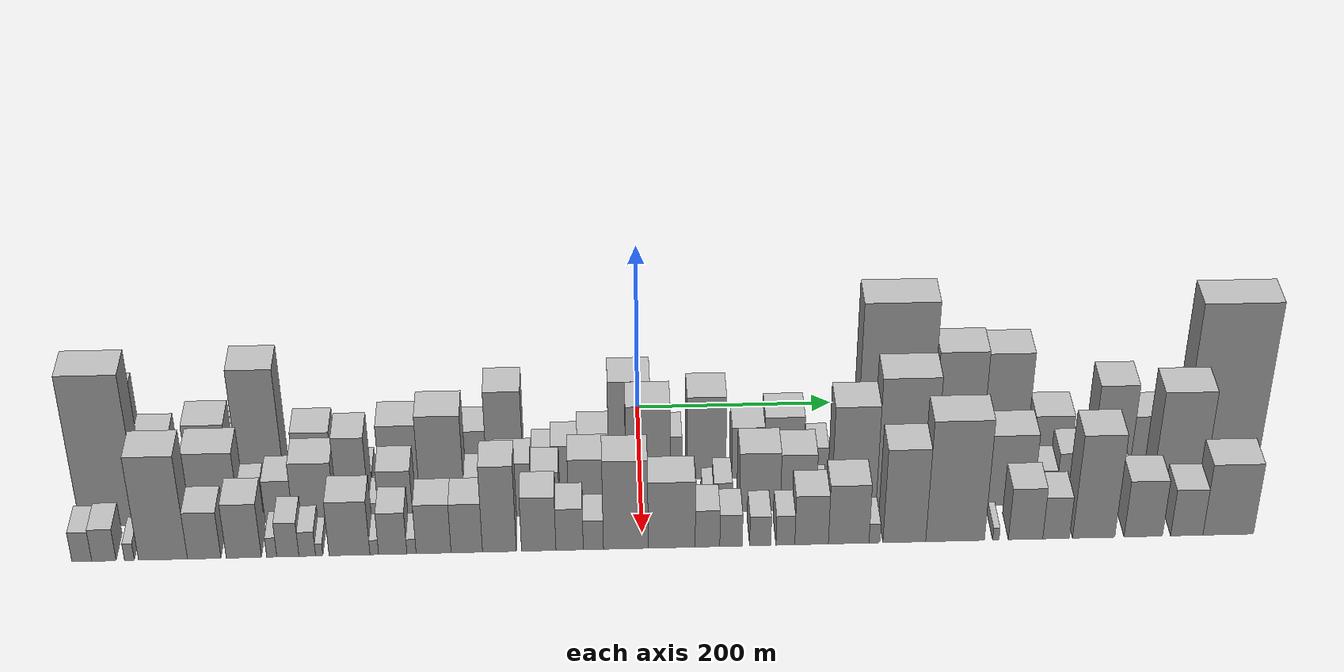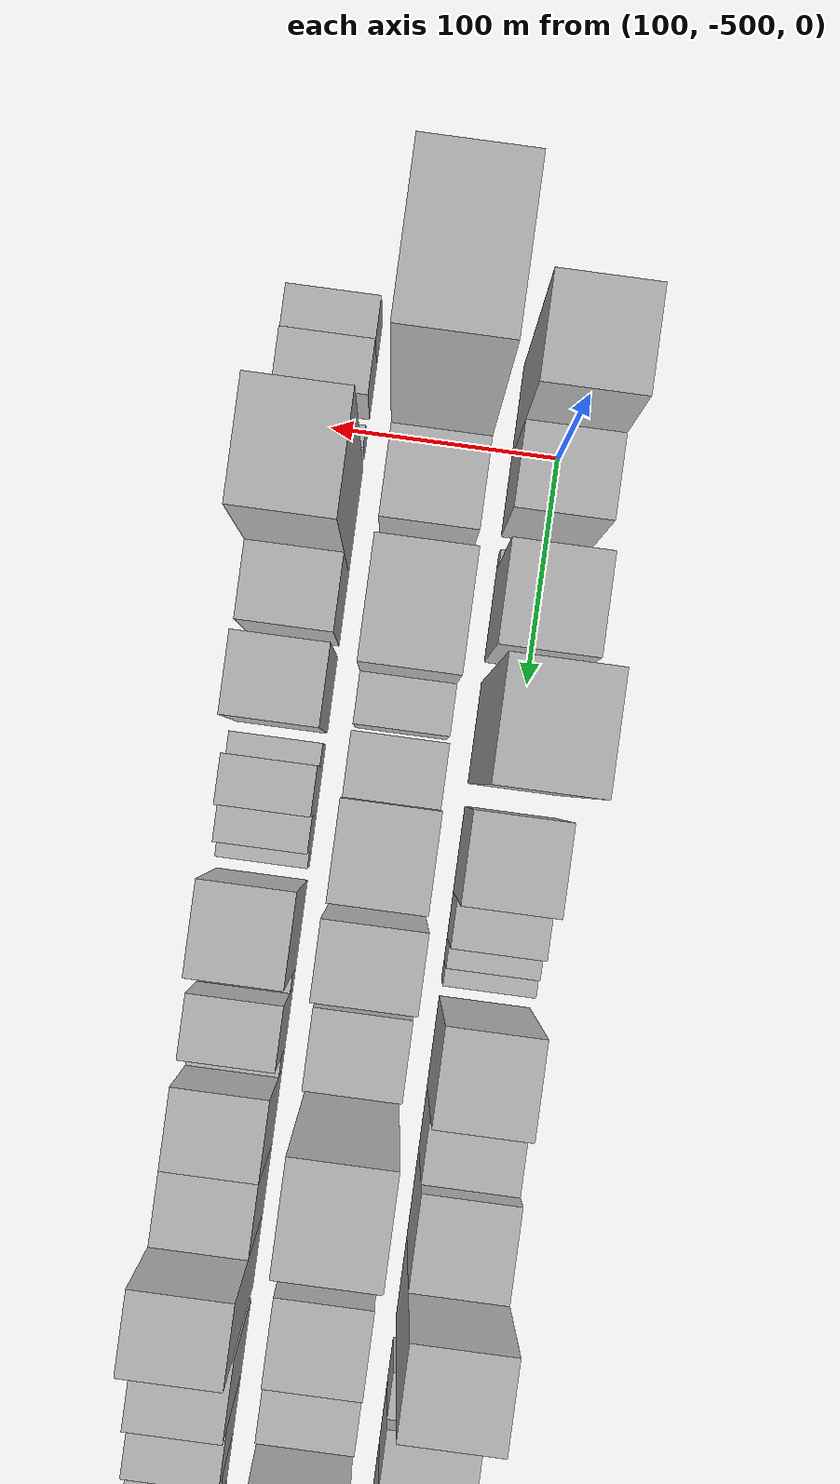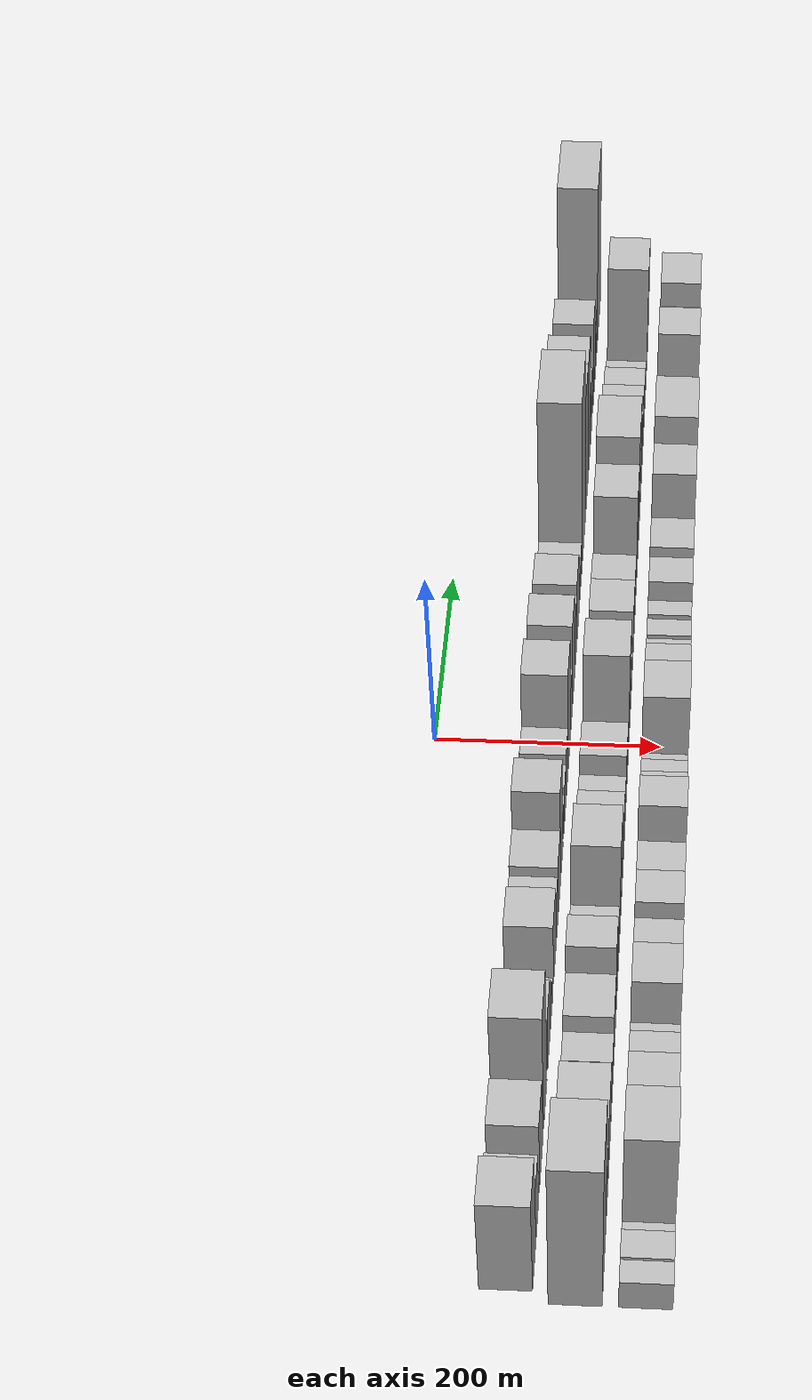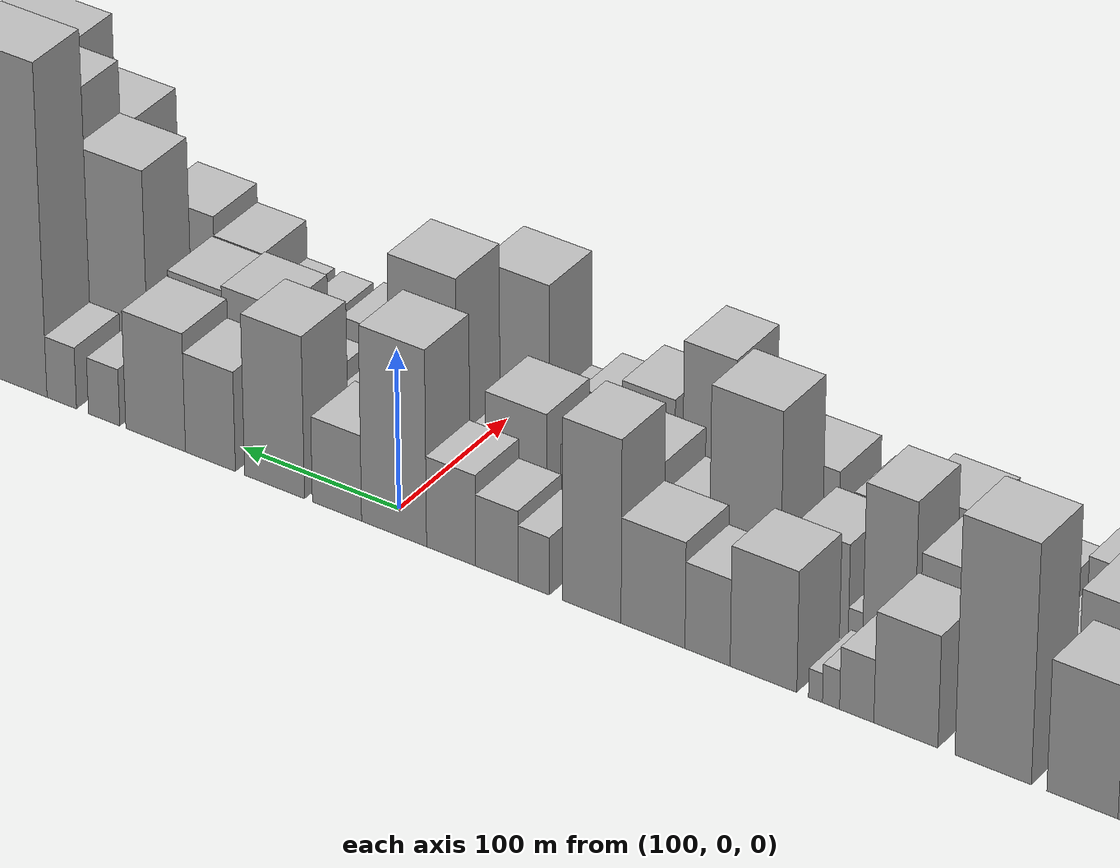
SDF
<sdf version="1.6">
 <world name="default">
  <scene>
   <sky><clouds><speed>12</speed></clouds></sky>
   <ambient>0.4 0.4 0.4 1</ambient>
   <background>0.7 0.7 0.7 1</background>
   <shadows>1</shadows>
  </scene>
  <gravity>0 0 -9.8066</gravity>
  <magnetic_field>6e-06 2.3e-05 -4.2e-05</magnetic_field>
  <physics default="0" name="default_physics" type="ode">
   <ode>
    <solver>
     <type>quick</type>
     <iters>10</iters>
     <sor>1.0</sor>
     <use_dynamic_moi_rescaling>0</use_dynamic_moi_rescaling>
    </solver>
    <constraints>
     <cfm>0</cfm>
     <erp>0.2</erp>
     <contact_max_correcting_vel>100</contact_max_correcting_vel>
     <contact_surface_layer>0.001</contact_surface_layer>
    </constraints>
   </ode>
   <max_step_size>0.004</max_step_size>
   <real_time_factor>1</real_time_factor>
   <real_time_update_rate>250</real_time_update_rate>
  </physics>
  <light name="sun" type="directional">
   <pose>0 0 10 0 0 0</pose>
   <diffuse>0.8 0.8 0.8 1</diffuse>
   <specular>0.2 0.2 0.2 1</specular>
   <attenuation>
    <range>1000</range>
    <constant>0.9</constant>
    <linear>0.01</linear>
    <quadratic>0.001</quadratic>
   </attenuation>
   <direction>-0.5 0.1 -0.9</direction>
  </light>
  <model name="building_1">
   <static>1</static>
   <pose>100.0000 -517.6219 0 0.000000 0.000000 0.000000</pose>
   <link name="link">
    <pose>0 0 58.50 0 0 0</pose>
    <collision name="collision"><geometry><box><size>40.0000 40.7561 117.0000</size></box></geometry></collision>
    <visual name="visual">
     <cast_shadows>0</cast_shadows>
     <geometry><box><size>40.0000 40.7561 117.0000</size></box></geometry>
     <material>
      <script>
       <uri>model://HANNAS_wall/materials/scripts</uri>
       <uri>model://HANNAS_wall/materials/textures</uri>
       <name>vrc/HANNAS_wall</name>
      </script>
     </material>
    </visual>
   </link>
  </model>
  <model name="building_2">
   <static>1</static>
   <pose>100.0000 -479.9347 0 0.000000 0.000000 0.000000</pose>
   <link name="link">
    <pose>0 0 33.00 0 0 0</pose>
    <collision name="collision"><geometry><box><size>40.0000 34.6183 66.0000</size></box></geometry></collision>
    <visual name="visual">
     <cast_shadows>0</cast_shadows>
     <geometry><box><size>40.0000 34.6183 66.0000</size></box></geometry>
     <material>
      <script>
       <uri>model://HANNAS_wall/materials/scripts</uri>
       <uri>model://HANNAS_wall/materials/textures</uri>
       <name>vrc/HANNAS_wall</name>
      </script>
     </material>
    </visual>
   </link>
  </model>
  <model name="building_3">
   <static>1</static>
   <pose>100.0000 -451.4299 0 0.000000 0.000000 0.000000</pose>
   <link name="link">
    <pose>0 0 7.50 0 0 0</pose>
    <collision name="collision"><geometry><box><size>40.0000 6.3911 15.0000</size></box></geometry></collision>
    <visual name="visual">
     <cast_shadows>0</cast_shadows>
     <geometry><box><size>40.0000 6.3911 15.0000</size></box></geometry>
     <material>
      <script>
       <uri>model://HANNAS_wall/materials/scripts</uri>
       <uri>model://HANNAS_wall/materials/textures</uri>
       <name>vrc/HANNAS_wall</name>
      </script>
     </material>
    </visual>
   </link>
  </model>
  <model name="building_4">
   <static>1</static>
   <pose>100.0000 -427.6770 0 0.000000 0.000000 0.000000</pose>
   <link name="link">
    <pose>0 0 40.50 0 0 0</pose>
    <collision name="collision"><geometry><box><size>40.0000 41.1148 81.0000</size></box></geometry></collision>
    <visual name="visual">
     <cast_shadows>0</cast_shadows>
     <geometry><box><size>40.0000 41.1148 81.0000</size></box></geometry>
     <material>
      <script>
       <uri>model://HANNAS_wall/materials/scripts</uri>
       <uri>model://HANNAS_wall/materials/textures</uri>
       <name>vrc/HANNAS_wall</name>
      </script>
     </material>
    </visual>
   </link>
  </model>
  <model name="building_5">
   <static>1</static>
   <pose>100.0000 -375.7939 0 0.000000 0.000000 0.000000</pose>
   <link name="link">
    <pose>0 0 73.50 0 0 0</pose>
    <collision name="collision"><geometry><box><size>40.0000 44.6514 147.0000</size></box></geometry></collision>
    <visual name="visual">
     <cast_shadows>0</cast_shadows>
     <geometry><box><size>40.0000 44.6514 147.0000</size></box></geometry>
     <material>
      <script>
       <uri>model://HANNAS_wall/materials/scripts</uri>
       <uri>model://HANNAS_wall/materials/textures</uri>
       <name>vrc/HANNAS_wall</name>
      </script>
     </material>
    </visual>
   </link>
  </model>
  <model name="building_6">
   <static>1</static>
   <pose>100.0000 -324.5157 0 0.000000 0.000000 0.000000</pose>
   <link name="link">
    <pose>0 0 34.50 0 0 0</pose>
    <collision name="collision"><geometry><box><size>40.0000 37.9049 69.0000</size></box></geometry></collision>
    <visual name="visual">
     <cast_shadows>0</cast_shadows>
     <geometry><box><size>40.0000 37.9049 69.0000</size></box></geometry>
     <material>
      <script>
       <uri>model://HANNAS_wall/materials/scripts</uri>
       <uri>model://HANNAS_wall/materials/textures</uri>
       <name>vrc/HANNAS_wall</name>
      </script>
     </material>
    </visual>
   </link>
  </model>
  <model name="building_7">
   <static>1</static>
   <pose>100.0000 -295.3833 0 0.000000 0.000000 0.000000</pose>
   <link name="link">
    <pose>0 0 19.50 0 0 0</pose>
    <collision name="collision"><geometry><box><size>40.0000 20.3600 39.0000</size></box></geometry></collision>
    <visual name="visual">
     <cast_shadows>0</cast_shadows>
     <geometry><box><size>40.0000 20.3600 39.0000</size></box></geometry>
     <material>
      <script>
       <uri>model://HANNAS_wall/materials/scripts</uri>
       <uri>model://HANNAS_wall/materials/textures</uri>
       <name>vrc/HANNAS_wall</name>
      </script>
     </material>
    </visual>
   </link>
  </model>
  <model name="building_8">
   <static>1</static>
   <pose>100.0000 -280.0929 0 0.000000 0.000000 0.000000</pose>
   <link name="link">
    <pose>0 0 12.00 0 0 0</pose>
    <collision name="collision"><geometry><box><size>40.0000 10.2207 24.0000</size></box></geometry></collision>
    <visual name="visual">
     <cast_shadows>0</cast_shadows>
     <geometry><box><size>40.0000 10.2207 24.0000</size></box></geometry>
     <material>
      <script>
       <uri>model://HANNAS_wall/materials/scripts</uri>
       <uri>model://HANNAS_wall/materials/textures</uri>
       <name>vrc/HANNAS_wall</name>
      </script>
     </material>
    </visual>
   </link>
  </model>
  <model name="building_9">
   <static>1</static>
   <pose>100.0000 -270.7997 0 0.000000 0.000000 0.000000</pose>
   <link name="link">
    <pose>0 0 9.00 0 0 0</pose>
    <collision name="collision"><geometry><box><size>40.0000 8.3657 18.0000</size></box></geometry></collision>
    <visual name="visual">
     <cast_shadows>0</cast_shadows>
     <geometry><box><size>40.0000 8.3657 18.0000</size></box></geometry>
     <material>
      <script>
       <uri>model://HANNAS_wall/materials/scripts</uri>
       <uri>model://HANNAS_wall/materials/textures</uri>
       <name>vrc/HANNAS_wall</name>
      </script>
     </material>
    </visual>
   </link>
  </model>
  <model name="building_10">
   <static>1</static>
   <pose>100.0000 -239.5225 0 0.000000 0.000000 0.000000</pose>
   <link name="link">
    <pose>0 0 37.50 0 0 0</pose>
    <collision name="collision"><geometry><box><size>40.0000 40.1889 75.0000</size></box></geometry></collision>
    <visual name="visual">
     <cast_shadows>0</cast_shadows>
     <geometry><box><size>40.0000 40.1889 75.0000</size></box></geometry>
     <material>
      <script>
       <uri>model://HANNAS_wall/materials/scripts</uri>
       <uri>model://HANNAS_wall/materials/textures</uri>
       <name>vrc/HANNAS_wall</name>
      </script>
     </material>
    </visual>
   </link>
  </model>
  <model name="building_11">
   <static>1</static>
   <pose>100.0000 -205.6912 0 0.000000 0.000000 0.000000</pose>
   <link name="link">
    <pose>0 0 27.00 0 0 0</pose>
    <collision name="collision"><geometry><box><size>40.0000 27.4736 54.0000</size></box></geometry></collision>
    <visual name="visual">
     <cast_shadows>0</cast_shadows>
     <geometry><box><size>40.0000 27.4736 54.0000</size></box></geometry>
     <material>
      <script>
       <uri>model://HANNAS_wall/materials/scripts</uri>
       <uri>model://HANNAS_wall/materials/textures</uri>
       <name>vrc/HANNAS_wall</name>
      </script>
     </material>
    </visual>
   </link>
  </model>
  <model name="building_12">
   <static>1</static>
   <pose>100.0000 -172.3648 0 0.000000 0.000000 0.000000</pose>
   <link name="link">
    <pose>0 0 33.00 0 0 0</pose>
    <collision name="collision"><geometry><box><size>40.0000 39.1793 66.0000</size></box></geometry></collision>
    <visual name="visual">
     <cast_shadows>0</cast_shadows>
     <geometry><box><size>40.0000 39.1793 66.0000</size></box></geometry>
     <material>
      <script>
       <uri>model://HANNAS_wall/materials/scripts</uri>
       <uri>model://HANNAS_wall/materials/textures</uri>
       <name>vrc/HANNAS_wall</name>
      </script>
     </material>
    </visual>
   </link>
  </model>
  <model name="building_13">
   <static>1</static>
   <pose>100.0000 -134.6445 0 0.000000 0.000000 0.000000</pose>
   <link name="link">
    <pose>0 0 57.00 0 0 0</pose>
    <collision name="collision"><geometry><box><size>40.0000 36.2613 114.0000</size></box></geometry></collision>
    <visual name="visual">
     <cast_shadows>0</cast_shadows>
     <geometry><box><size>40.0000 36.2613 114.0000</size></box></geometry>
     <material>
      <script>
       <uri>model://HANNAS_wall/materials/scripts</uri>
       <uri>model://HANNAS_wall/materials/textures</uri>
       <name>vrc/HANNAS_wall</name>
      </script>
     </material>
    </visual>
   </link>
  </model>
  <model name="building_14">
   <static>1</static>
   <pose>100.0000 -98.7660 0 0.000000 0.000000 0.000000</pose>
   <link name="link">
    <pose>0 0 18.00 0 0 0</pose>
    <collision name="collision"><geometry><box><size>40.0000 19.4958 36.0000</size></box></geometry></collision>
    <visual name="visual">
     <cast_shadows>0</cast_shadows>
     <geometry><box><size>40.0000 19.4958 36.0000</size></box></geometry>
     <material>
      <script>
       <uri>model://HANNAS_wall/materials/scripts</uri>
       <uri>model://HANNAS_wall/materials/textures</uri>
       <name>vrc/HANNAS_wall</name>
      </script>
     </material>
    </visual>
   </link>
  </model>
  <model name="building_15">
   <static>1</static>
   <pose>100.0000 -75.7453 0 0.000000 0.000000 0.000000</pose>
   <link name="link">
    <pose>0 0 22.50 0 0 0</pose>
    <collision name="collision"><geometry><box><size>40.0000 26.5456 45.0000</size></box></geometry></collision>
    <visual name="visual">
     <cast_shadows>0</cast_shadows>
     <geometry><box><size>40.0000 26.5456 45.0000</size></box></geometry>
     <material>
      <script>
       <uri>model://HANNAS_wall/materials/scripts</uri>
       <uri>model://HANNAS_wall/materials/textures</uri>
       <name>vrc/HANNAS_wall</name>
      </script>
     </material>
    </visual>
   </link>
  </model>
  <model name="building_16">
   <static>1</static>
   <pose>100.0000 -46.9878 0 0.000000 0.000000 0.000000</pose>
   <link name="link">
    <pose>0 0 28.50 0 0 0</pose>
    <collision name="collision"><geometry><box><size>40.0000 30.9693 57.0000</size></box></geometry></collision>
    <visual name="visual">
     <cast_shadows>0</cast_shadows>
     <geometry><box><size>40.0000 30.9693 57.0000</size></box></geometry>
     <material>
      <script>
       <uri>model://HANNAS_wall/materials/scripts</uri>
       <uri>model://HANNAS_wall/materials/textures</uri>
       <name>vrc/HANNAS_wall</name>
      </script>
     </material>
    </visual>
   </link>
  </model>
  <model name="building_17">
   <static>1</static>
   <pose>100.0000 -10.8562 0 0.000000 0.000000 0.000000</pose>
   <link name="link">
    <pose>0 0 61.50 0 0 0</pose>
    <collision name="collision"><geometry><box><size>40.0000 41.2940 123.0000</size></box></geometry></collision>
    <visual name="visual">
     <cast_shadows>0</cast_shadows>
     <geometry><box><size>40.0000 41.2940 123.0000</size></box></geometry>
     <material>
      <script>
       <uri>model://HANNAS_wall/materials/scripts</uri>
       <uri>model://HANNAS_wall/materials/textures</uri>
       <name>vrc/HANNAS_wall</name>
      </script>
     </material>
    </visual>
   </link>
  </model>
  <model name="building_18">
   <static>1</static>
   <pose>100.0000 25.5710 0 0.000000 0.000000 0.000000</pose>
   <link name="link">
    <pose>0 0 27.00 0 0 0</pose>
    <collision name="collision"><geometry><box><size>40.0000 31.5603 54.0000</size></box></geometry></collision>
    <visual name="visual">
     <cast_shadows>0</cast_shadows>
     <geometry><box><size>40.0000 31.5603 54.0000</size></box></geometry>
     <material>
      <script>
       <uri>model://HANNAS_wall/materials/scripts</uri>
       <uri>model://HANNAS_wall/materials/textures</uri>
       <name>vrc/HANNAS_wall</name>
      </script>
     </material>
    </visual>
   </link>
  </model>
  <model name="building_19">
   <static>1</static>
   <pose>100.0000 65.7155 0 0.000000 0.000000 0.000000</pose>
   <link name="link">
    <pose>0 0 51.00 0 0 0</pose>
    <collision name="collision"><geometry><box><size>40.0000 38.7289 102.0000</size></box></geometry></collision>
    <visual name="visual">
     <cast_shadows>0</cast_shadows>
     <geometry><box><size>40.0000 38.7289 102.0000</size></box></geometry>
     <material>
      <script>
       <uri>model://HANNAS_wall/materials/scripts</uri>
       <uri>model://HANNAS_wall/materials/textures</uri>
       <name>vrc/HANNAS_wall</name>
      </script>
     </material>
    </visual>
   </link>
  </model>
  <model name="building_20">
   <static>1</static>
   <pose>100.0000 107.3781 0 0.000000 0.000000 0.000000</pose>
   <link name="link">
    <pose>0 0 31.50 0 0 0</pose>
    <collision name="collision"><geometry><box><size>40.0000 32.5962 63.0000</size></box></geometry></collision>
    <visual name="visual">
     <cast_shadows>0</cast_shadows>
     <geometry><box><size>40.0000 32.5962 63.0000</size></box></geometry>
     <material>
      <script>
       <uri>model://HANNAS_wall/materials/scripts</uri>
       <uri>model://HANNAS_wall/materials/textures</uri>
       <name>vrc/HANNAS_wall</name>
      </script>
     </material>
    </visual>
   </link>
  </model>
  <model name="building_21">
   <static>1</static>
   <pose>100.0000 143.3019 0 0.000000 0.000000 0.000000</pose>
   <link name="link">
    <pose>0 0 37.50 0 0 0</pose>
    <collision name="collision"><geometry><box><size>40.0000 39.2515 75.0000</size></box></geometry></collision>
    <visual name="visual">
     <cast_shadows>0</cast_shadows>
     <geometry><box><size>40.0000 39.2515 75.0000</size></box></geometry>
     <material>
      <script>
       <uri>model://HANNAS_wall/materials/scripts</uri>
       <uri>model://HANNAS_wall/materials/textures</uri>
       <name>vrc/HANNAS_wall</name>
      </script>
     </material>
    </visual>
   </link>
  </model>
  <model name="building_22">
   <static>1</static>
   <pose>100.0000 177.2840 0 0.000000 0.000000 0.000000</pose>
   <link name="link">
    <pose>0 0 18.00 0 0 0</pose>
    <collision name="collision"><geometry><box><size>40.0000 20.7128 36.0000</size></box></geometry></collision>
    <visual name="visual">
     <cast_shadows>0</cast_shadows>
     <geometry><box><size>40.0000 20.7128 36.0000</size></box></geometry>
     <material>
      <script>
       <uri>model://HANNAS_wall/materials/scripts</uri>
       <uri>model://HANNAS_wall/materials/textures</uri>
       <name>vrc/HANNAS_wall</name>
      </script>
     </material>
    </visual>
   </link>
  </model>
  <model name="building_23">
   <static>1</static>
   <pose>100.0000 205.4724 0 0.000000 0.000000 0.000000</pose>
   <link name="link">
    <pose>0 0 19.50 0 0 0</pose>
    <collision name="collision"><geometry><box><size>40.0000 19.6639 39.0000</size></box></geometry></collision>
    <visual name="visual">
     <cast_shadows>0</cast_shadows>
     <geometry><box><size>40.0000 19.6639 39.0000</size></box></geometry>
     <material>
      <script>
       <uri>model://HANNAS_wall/materials/scripts</uri>
       <uri>model://HANNAS_wall/materials/textures</uri>
       <name>vrc/HANNAS_wall</name>
      </script>
     </material>
    </visual>
   </link>
  </model>
  <model name="building_24">
   <static>1</static>
   <pose>100.0000 251.9849 0 0.000000 0.000000 0.000000</pose>
   <link name="link">
    <pose>0 0 105.00 0 0 0</pose>
    <collision name="collision"><geometry><box><size>40.0000 73.3611 210.0000</size></box></geometry></collision>
    <visual name="visual">
     <cast_shadows>0</cast_shadows>
     <geometry><box><size>40.0000 73.3611 210.0000</size></box></geometry>
     <material>
      <script>
       <uri>model://HANNAS_wall/materials/scripts</uri>
       <uri>model://HANNAS_wall/materials/textures</uri>
       <name>vrc/HANNAS_wall</name>
      </script>
     </material>
    </visual>
   </link>
  </model>
  <model name="building_25">
   <static>1</static>
   <pose>100.0000 315.9877 0 0.000000 0.000000 0.000000</pose>
   <link name="link">
    <pose>0 0 75.00 0 0 0</pose>
    <collision name="collision"><geometry><box><size>40.0000 48.6444 150.0000</size></box></geometry></collision>
    <visual name="visual">
     <cast_shadows>0</cast_shadows>
     <geometry><box><size>40.0000 48.6444 150.0000</size></box></geometry>
     <material>
      <script>
       <uri>model://HANNAS_wall/materials/scripts</uri>
       <uri>model://HANNAS_wall/materials/textures</uri>
       <name>vrc/HANNAS_wall</name>
      </script>
     </material>
    </visual>
   </link>
  </model>
  <model name="building_26">
   <static>1</static>
   <pose>100.0000 362.5225 0 0.000000 0.000000 0.000000</pose>
   <link name="link">
    <pose>0 0 73.50 0 0 0</pose>
    <collision name="collision"><geometry><box><size>40.0000 44.4252 147.0000</size></box></geometry></collision>
    <visual name="visual">
     <cast_shadows>0</cast_shadows>
     <geometry><box><size>40.0000 44.4252 147.0000</size></box></geometry>
     <material>
      <script>
       <uri>model://HANNAS_wall/materials/scripts</uri>
       <uri>model://HANNAS_wall/materials/textures</uri>
       <name>vrc/HANNAS_wall</name>
      </script>
     </material>
    </visual>
   </link>
  </model>
  <model name="building_27">
   <static>1</static>
   <pose>100.0000 388.2325 0 0.000000 0.000000 0.000000</pose>
   <link name="link">
    <pose>0 0 7.50 0 0 0</pose>
    <collision name="collision"><geometry><box><size>40.0000 6.9949 15.0000</size></box></geometry></collision>
    <visual name="visual">
     <cast_shadows>0</cast_shadows>
     <geometry><box><size>40.0000 6.9949 15.0000</size></box></geometry>
     <material>
      <script>
       <uri>model://HANNAS_wall/materials/scripts</uri>
       <uri>model://HANNAS_wall/materials/textures</uri>
       <name>vrc/HANNAS_wall</name>
      </script>
     </material>
    </visual>
   </link>
  </model>
  <model name="building_28">
   <static>1</static>
   <pose>100.0000 411.1243 0 0.000000 0.000000 0.000000</pose>
   <link name="link">
    <pose>0 0 34.50 0 0 0</pose>
    <collision name="collision"><geometry><box><size>40.0000 38.7887 69.0000</size></box></geometry></collision>
    <visual name="visual">
     <cast_shadows>0</cast_shadows>
     <geometry><box><size>40.0000 38.7887 69.0000</size></box></geometry>
     <material>
      <script>
       <uri>model://HANNAS_wall/materials/scripts</uri>
       <uri>model://HANNAS_wall/materials/textures</uri>
       <name>vrc/HANNAS_wall</name>
      </script>
     </material>
    </visual>
   </link>
  </model>
  <model name="building_29">
   <static>1</static>
   <pose>100.0000 446.5157 0 0.000000 0.000000 0.000000</pose>
   <link name="link">
    <pose>0 0 12.00 0 0 0</pose>
    <collision name="collision"><geometry><box><size>40.0000 11.9940 24.0000</size></box></geometry></collision>
    <visual name="visual">
     <cast_shadows>0</cast_shadows>
     <geometry><box><size>40.0000 11.9940 24.0000</size></box></geometry>
     <material>
      <script>
       <uri>model://HANNAS_wall/materials/scripts</uri>
       <uri>model://HANNAS_wall/materials/textures</uri>
       <name>vrc/HANNAS_wall</name>
      </script>
     </material>
    </visual>
   </link>
  </model>
  <model name="building_30">
   <static>1</static>
   <pose>100.0000 471.8779 0 0.000000 0.000000 0.000000</pose>
   <link name="link">
    <pose>0 0 52.50 0 0 0</pose>
    <collision name="collision"><geometry><box><size>40.0000 38.7305 105.0000</size></box></geometry></collision>
    <visual name="visual">
     <cast_shadows>0</cast_shadows>
     <geometry><box><size>40.0000 38.7305 105.0000</size></box></geometry>
     <material>
      <script>
       <uri>model://HANNAS_wall/materials/scripts</uri>
       <uri>model://HANNAS_wall/materials/textures</uri>
       <name>vrc/HANNAS_wall</name>
      </script>
     </material>
    </visual>
   </link>
  </model>
  <model name="building_31">
   <static>1</static>
   <pose>100.0000 507.8915 0 0.000000 0.000000 0.000000</pose>
   <link name="link">
    <pose>0 0 33.00 0 0 0</pose>
    <collision name="collision"><geometry><box><size>40.0000 33.2967 66.0000</size></box></geometry></collision>
    <visual name="visual">
     <cast_shadows>0</cast_shadows>
     <geometry><box><size>40.0000 33.2967 66.0000</size></box></geometry>
     <material>
      <script>
       <uri>model://HANNAS_wall/materials/scripts</uri>
       <uri>model://HANNAS_wall/materials/textures</uri>
       <name>vrc/HANNAS_wall</name>
      </script>
     </material>
    </visual>
   </link>
  </model>
  <model name="building_32">
   <static>1</static>
   <pose>100.0000 533.4100 0 0.000000 0.000000 0.000000</pose>
   <link name="link">
    <pose>0 0 15.00 0 0 0</pose>
    <collision name="collision"><geometry><box><size>40.0000 17.7402 30.0000</size></box></geometry></collision>
    <visual name="visual">
     <cast_shadows>0</cast_shadows>
     <geometry><box><size>40.0000 17.7402 30.0000</size></box></geometry>
     <material>
      <script>
       <uri>model://HANNAS_wall/materials/scripts</uri>
       <uri>model://HANNAS_wall/materials/textures</uri>
       <name>vrc/HANNAS_wall</name>
      </script>
     </material>
    </visual>
   </link>
  </model>
  <model name="building_33">
   <static>1</static>
   <pose>100.0000 581.3215 0 0.000000 0.000000 0.000000</pose>
   <link name="link">
    <pose>0 0 100.50 0 0 0</pose>
    <collision name="collision"><geometry><box><size>40.0000 78.0828 201.0000</size></box></geometry></collision>
    <visual name="visual">
     <cast_shadows>0</cast_shadows>
     <geometry><box><size>40.0000 78.0828 201.0000</size></box></geometry>
     <material>
      <script>
       <uri>model://HANNAS_wall/materials/scripts</uri>
       <uri>model://HANNAS_wall/materials/textures</uri>
       <name>vrc/HANNAS_wall</name>
      </script>
     </material>
    </visual>
   </link>
  </model>
  <model name="building_34">
   <static>1</static>
   <pose>152.0000 -518.4679 0 0.000000 0.000000 0.000000</pose>
   <link name="link">
    <pose>0 0 91.50 0 0 0</pose>
    <collision name="collision"><geometry><box><size>40.0000 59.0643 183.0000</size></box></geometry></collision>
    <visual name="visual">
     <cast_shadows>0</cast_shadows>
     <geometry><box><size>40.0000 59.0643 183.0000</size></box></geometry>
     <material>
      <script>
       <uri>model://HANNAS_wall/materials/scripts</uri>
       <uri>model://HANNAS_wall/materials/textures</uri>
       <name>vrc/HANNAS_wall</name>
      </script>
     </material>
    </visual>
   </link>
  </model>
  <model name="building_35">
   <static>1</static>
   <pose>152.0000 -470.4753 0 0.000000 0.000000 0.000000</pose>
   <link name="link">
    <pose>0 0 33.00 0 0 0</pose>
    <collision name="collision"><geometry><box><size>40.0000 36.9209 66.0000</size></box></geometry></collision>
    <visual name="visual">
     <cast_shadows>0</cast_shadows>
     <geometry><box><size>40.0000 36.9209 66.0000</size></box></geometry>
     <material>
      <script>
       <uri>model://HANNAS_wall/materials/scripts</uri>
       <uri>model://HANNAS_wall/materials/textures</uri>
       <name>vrc/HANNAS_wall</name>
      </script>
     </material>
    </visual>
   </link>
  </model>
  <model name="building_36">
   <static>1</static>
   <pose>152.0000 -417.4977 0 0.000000 0.000000 0.000000</pose>
   <link name="link">
    <pose>0 0 43.50 0 0 0</pose>
    <collision name="collision"><geometry><box><size>40.0000 49.0343 87.0000</size></box></geometry></collision>
    <visual name="visual">
     <cast_shadows>0</cast_shadows>
     <geometry><box><size>40.0000 49.0343 87.0000</size></box></geometry>
     <material>
      <script>
       <uri>model://HANNAS_wall/materials/scripts</uri>
       <uri>model://HANNAS_wall/materials/textures</uri>
       <name>vrc/HANNAS_wall</name>
      </script>
     </material>
    </visual>
   </link>
  </model>
  <model name="building_37">
   <static>1</static>
   <pose>152.0000 -382.1001 0 0.000000 0.000000 0.000000</pose>
   <link name="link">
    <pose>0 0 21.00 0 0 0</pose>
    <collision name="collision"><geometry><box><size>40.0000 21.7610 42.0000</size></box></geometry></collision>
    <visual name="visual">
     <cast_shadows>0</cast_shadows>
     <geometry><box><size>40.0000 21.7610 42.0000</size></box></geometry>
     <material>
      <script>
       <uri>model://HANNAS_wall/materials/scripts</uri>
       <uri>model://HANNAS_wall/materials/textures</uri>
       <name>vrc/HANNAS_wall</name>
      </script>
     </material>
    </visual>
   </link>
  </model>
  <model name="building_38">
   <static>1</static>
   <pose>152.0000 -354.6735 0 0.000000 0.000000 0.000000</pose>
   <link name="link">
    <pose>0 0 25.50 0 0 0</pose>
    <collision name="collision"><geometry><box><size>40.0000 27.0921 51.0000</size></box></geometry></collision>
    <visual name="visual">
     <cast_shadows>0</cast_shadows>
     <geometry><box><size>40.0000 27.0921 51.0000</size></box></geometry>
     <material>
      <script>
       <uri>model://HANNAS_wall/materials/scripts</uri>
       <uri>model://HANNAS_wall/materials/textures</uri>
       <name>vrc/HANNAS_wall</name>
      </script>
     </material>
    </visual>
   </link>
  </model>
  <model name="building_39">
   <static>1</static>
   <pose>152.0000 -320.5675 0 0.000000 0.000000 0.000000</pose>
   <link name="link">
    <pose>0 0 36.00 0 0 0</pose>
    <collision name="collision"><geometry><box><size>40.0000 41.1198 72.0000</size></box></geometry></collision>
    <visual name="visual">
     <cast_shadows>0</cast_shadows>
     <geometry><box><size>40.0000 41.1198 72.0000</size></box></geometry>
     <material>
      <script>
       <uri>model://HANNAS_wall/materials/scripts</uri>
       <uri>model://HANNAS_wall/materials/textures</uri>
       <name>vrc/HANNAS_wall</name>
      </script>
     </material>
    </visual>
   </link>
  </model>
  <model name="building_40">
   <static>1</static>
   <pose>152.0000 -281.5517 0 0.000000 0.000000 0.000000</pose>
   <link name="link">
    <pose>0 0 51.00 0 0 0</pose>
    <collision name="collision"><geometry><box><size>40.0000 30.9117 102.0000</size></box></geometry></collision>
    <visual name="visual">
     <cast_shadows>0</cast_shadows>
     <geometry><box><size>40.0000 30.9117 102.0000</size></box></geometry>
     <material>
      <script>
       <uri>model://HANNAS_wall/materials/scripts</uri>
       <uri>model://HANNAS_wall/materials/textures</uri>
       <name>vrc/HANNAS_wall</name>
      </script>
     </material>
    </visual>
   </link>
  </model>
  <model name="building_41">
   <static>1</static>
   <pose>152.0000 -261.7792 0 0.000000 0.000000 0.000000</pose>
   <link name="link">
    <pose>0 0 10.50 0 0 0</pose>
    <collision name="collision"><geometry><box><size>40.0000 8.6333 21.0000</size></box></geometry></collision>
    <visual name="visual">
     <cast_shadows>0</cast_shadows>
     <geometry><box><size>40.0000 8.6333 21.0000</size></box></geometry>
     <material>
      <script>
       <uri>model://HANNAS_wall/materials/scripts</uri>
       <uri>model://HANNAS_wall/materials/textures</uri>
       <name>vrc/HANNAS_wall</name>
      </script>
     </material>
    </visual>
   </link>
  </model>
  <model name="building_42">
   <static>1</static>
   <pose>152.0000 -240.7744 0 0.000000 0.000000 0.000000</pose>
   <link name="link">
    <pose>0 0 30.00 0 0 0</pose>
    <collision name="collision"><geometry><box><size>40.0000 33.3762 60.0000</size></box></geometry></collision>
    <visual name="visual">
     <cast_shadows>0</cast_shadows>
     <geometry><box><size>40.0000 33.3762 60.0000</size></box></geometry>
     <material>
      <script>
       <uri>model://HANNAS_wall/materials/scripts</uri>
       <uri>model://HANNAS_wall/materials/textures</uri>
       <name>vrc/HANNAS_wall</name>
      </script>
     </material>
    </visual>
   </link>
  </model>
  <model name="building_43">
   <static>1</static>
   <pose>152.0000 -194.4252 0 0.000000 0.000000 0.000000</pose>
   <link name="link">
    <pose>0 0 63.00 0 0 0</pose>
    <collision name="collision"><geometry><box><size>40.0000 43.3221 126.0000</size></box></geometry></collision>
    <visual name="visual">
     <cast_shadows>0</cast_shadows>
     <geometry><box><size>40.0000 43.3221 126.0000</size></box></geometry>
     <material>
      <script>
       <uri>model://HANNAS_wall/materials/scripts</uri>
       <uri>model://HANNAS_wall/materials/textures</uri>
       <name>vrc/HANNAS_wall</name>
      </script>
     </material>
    </visual>
   </link>
  </model>
  <model name="building_44">
   <static>1</static>
   <pose>152.0000 -158.3745 0 0.000000 0.000000 0.000000</pose>
   <link name="link">
    <pose>0 0 24.00 0 0 0</pose>
    <collision name="collision"><geometry><box><size>40.0000 28.7794 48.0000</size></box></geometry></collision>
    <visual name="visual">
     <cast_shadows>0</cast_shadows>
     <geometry><box><size>40.0000 28.7794 48.0000</size></box></geometry>
     <material>
      <script>
       <uri>model://HANNAS_wall/materials/scripts</uri>
       <uri>model://HANNAS_wall/materials/textures</uri>
       <name>vrc/HANNAS_wall</name>
      </script>
     </material>
    </visual>
   </link>
  </model>
  <model name="building_45">
   <static>1</static>
   <pose>152.0000 -125.9204 0 0.000000 0.000000 0.000000</pose>
   <link name="link">
    <pose>0 0 33.00 0 0 0</pose>
    <collision name="collision"><geometry><box><size>40.0000 36.1287 66.0000</size></box></geometry></collision>
    <visual name="visual">
     <cast_shadows>0</cast_shadows>
     <geometry><box><size>40.0000 36.1287 66.0000</size></box></geometry>
     <material>
      <script>
       <uri>model://HANNAS_wall/materials/scripts</uri>
       <uri>model://HANNAS_wall/materials/textures</uri>
       <name>vrc/HANNAS_wall</name>
      </script>
     </material>
    </visual>
   </link>
  </model>
  <model name="building_46">
   <static>1</static>
   <pose>152.0000 -94.2431 0 0.000000 0.000000 0.000000</pose>
   <link name="link">
    <pose>0 0 27.00 0 0 0</pose>
    <collision name="collision"><geometry><box><size>40.0000 27.2260 54.0000</size></box></geometry></collision>
    <visual name="visual">
     <cast_shadows>0</cast_shadows>
     <geometry><box><size>40.0000 27.2260 54.0000</size></box></geometry>
     <material>
      <script>
       <uri>model://HANNAS_wall/materials/scripts</uri>
       <uri>model://HANNAS_wall/materials/textures</uri>
       <name>vrc/HANNAS_wall</name>
      </script>
     </material>
    </visual>
   </link>
  </model>
  <model name="building_47">
   <static>1</static>
   <pose>152.0000 -52.3429 0 0.000000 0.000000 0.000000</pose>
   <link name="link">
    <pose>0 0 34.50 0 0 0</pose>
    <collision name="collision"><geometry><box><size>40.0000 38.5744 69.0000</size></box></geometry></collision>
    <visual name="visual">
     <cast_shadows>0</cast_shadows>
     <geometry><box><size>40.0000 38.5744 69.0000</size></box></geometry>
     <material>
      <script>
       <uri>model://HANNAS_wall/materials/scripts</uri>
       <uri>model://HANNAS_wall/materials/textures</uri>
       <name>vrc/HANNAS_wall</name>
      </script>
     </material>
    </visual>
   </link>
  </model>
  <model name="building_48">
   <static>1</static>
   <pose>152.0000 -23.9914 0 0.000000 0.000000 0.000000</pose>
   <link name="link">
    <pose>0 0 16.50 0 0 0</pose>
    <collision name="collision"><geometry><box><size>40.0000 18.1285 33.0000</size></box></geometry></collision>
    <visual name="visual">
     <cast_shadows>0</cast_shadows>
     <geometry><box><size>40.0000 18.1285 33.0000</size></box></geometry>
     <material>
      <script>
       <uri>model://HANNAS_wall/materials/scripts</uri>
       <uri>model://HANNAS_wall/materials/textures</uri>
       <name>vrc/HANNAS_wall</name>
      </script>
     </material>
    </visual>
   </link>
  </model>
  <model name="building_49">
   <static>1</static>
   <pose>152.0000 6.5699 0 0.000000 0.000000 0.000000</pose>
   <link name="link">
    <pose>0 0 66.00 0 0 0</pose>
    <collision name="collision"><geometry><box><size>40.0000 42.9942 132.0000</size></box></geometry></collision>
    <visual name="visual">
     <cast_shadows>0</cast_shadows>
     <geometry><box><size>40.0000 42.9942 132.0000</size></box></geometry>
     <material>
      <script>
       <uri>model://HANNAS_wall/materials/scripts</uri>
       <uri>model://HANNAS_wall/materials/textures</uri>
       <name>vrc/HANNAS_wall</name>
      </script>
     </material>
    </visual>
   </link>
  </model>
  <model name="building_50">
   <static>1</static>
   <pose>152.0000 44.9130 0 0.000000 0.000000 0.000000</pose>
   <link name="link">
    <pose>0 0 15.00 0 0 0</pose>
    <collision name="collision"><geometry><box><size>40.0000 17.6921 30.0000</size></box></geometry></collision>
    <visual name="visual">
     <cast_shadows>0</cast_shadows>
     <geometry><box><size>40.0000 17.6921 30.0000</size></box></geometry>
     <material>
      <script>
       <uri>model://HANNAS_wall/materials/scripts</uri>
       <uri>model://HANNAS_wall/materials/textures</uri>
       <name>vrc/HANNAS_wall</name>
      </script>
     </material>
    </visual>
   </link>
  </model>
  <model name="building_51">
   <static>1</static>
   <pose>152.0000 65.2904 0 0.000000 0.000000 0.000000</pose>
   <link name="link">
    <pose>0 0 12.00 0 0 0</pose>
    <collision name="collision"><geometry><box><size>40.0000 11.0626 24.0000</size></box></geometry></collision>
    <visual name="visual">
     <cast_shadows>0</cast_shadows>
     <geometry><box><size>40.0000 11.0626 24.0000</size></box></geometry>
     <material>
      <script>
       <uri>model://HANNAS_wall/materials/scripts</uri>
       <uri>model://HANNAS_wall/materials/textures</uri>
       <name>vrc/HANNAS_wall</name>
      </script>
     </material>
    </visual>
   </link>
  </model>
  <model name="building_52">
   <static>1</static>
   <pose>152.0000 79.8577 0 0.000000 0.000000 0.000000</pose>
   <link name="link">
    <pose>0 0 18.00 0 0 0</pose>
    <collision name="collision"><geometry><box><size>40.0000 18.0720 36.0000</size></box></geometry></collision>
    <visual name="visual">
     <cast_shadows>0</cast_shadows>
     <geometry><box><size>40.0000 18.0720 36.0000</size></box></geometry>
     <material>
      <script>
       <uri>model://HANNAS_wall/materials/scripts</uri>
       <uri>model://HANNAS_wall/materials/textures</uri>
       <name>vrc/HANNAS_wall</name>
      </script>
     </material>
    </visual>
   </link>
  </model>
  <model name="building_53">
   <static>1</static>
   <pose>152.0000 116.0636 0 0.000000 0.000000 0.000000</pose>
   <link name="link">
    <pose>0 0 36.00 0 0 0</pose>
    <collision name="collision"><geometry><box><size>40.0000 40.3400 72.0000</size></box></geometry></collision>
    <visual name="visual">
     <cast_shadows>0</cast_shadows>
     <geometry><box><size>40.0000 40.3400 72.0000</size></box></geometry>
     <material>
      <script>
       <uri>model://HANNAS_wall/materials/scripts</uri>
       <uri>model://HANNAS_wall/materials/textures</uri>
       <name>vrc/HANNAS_wall</name>
      </script>
     </material>
    </visual>
   </link>
  </model>
  <model name="building_54">
   <static>1</static>
   <pose>152.0000 153.8333 0 0.000000 0.000000 0.000000</pose>
   <link name="link">
    <pose>0 0 34.50 0 0 0</pose>
    <collision name="collision"><geometry><box><size>40.0000 35.1993 69.0000</size></box></geometry></collision>
    <visual name="visual">
     <cast_shadows>0</cast_shadows>
     <geometry><box><size>40.0000 35.1993 69.0000</size></box></geometry>
     <material>
      <script>
       <uri>model://HANNAS_wall/materials/scripts</uri>
       <uri>model://HANNAS_wall/materials/textures</uri>
       <name>vrc/HANNAS_wall</name>
      </script>
     </material>
    </visual>
   </link>
  </model>
  <model name="building_55">
   <static>1</static>
   <pose>152.0000 176.9388 0 0.000000 0.000000 0.000000</pose>
   <link name="link">
    <pose>0 0 12.00 0 0 0</pose>
    <collision name="collision"><geometry><box><size>40.0000 11.0118 24.0000</size></box></geometry></collision>
    <visual name="visual">
     <cast_shadows>0</cast_shadows>
     <geometry><box><size>40.0000 11.0118 24.0000</size></box></geometry>
     <material>
      <script>
       <uri>model://HANNAS_wall/materials/scripts</uri>
       <uri>model://HANNAS_wall/materials/textures</uri>
       <name>vrc/HANNAS_wall</name>
      </script>
     </material>
    </visual>
   </link>
  </model>
  <model name="building_56">
   <static>1</static>
   <pose>152.0000 208.4596 0 0.000000 0.000000 0.000000</pose>
   <link name="link">
    <pose>0 0 63.00 0 0 0</pose>
    <collision name="collision"><geometry><box><size>40.0000 44.0297 126.0000</size></box></geometry></collision>
    <visual name="visual">
     <cast_shadows>0</cast_shadows>
     <geometry><box><size>40.0000 44.0297 126.0000</size></box></geometry>
     <material>
      <script>
       <uri>model://HANNAS_wall/materials/scripts</uri>
       <uri>model://HANNAS_wall/materials/textures</uri>
       <name>vrc/HANNAS_wall</name>
      </script>
     </material>
    </visual>
   </link>
  </model>
  <model name="building_57">
   <static>1</static>
   <pose>152.0000 258.8494 0 0.000000 0.000000 0.000000</pose>
   <link name="link">
    <pose>0 0 79.50 0 0 0</pose>
    <collision name="collision"><geometry><box><size>40.0000 56.7500 159.0000</size></box></geometry></collision>
    <visual name="visual">
     <cast_shadows>0</cast_shadows>
     <geometry><box><size>40.0000 56.7500 159.0000</size></box></geometry>
     <material>
      <script>
       <uri>model://HANNAS_wall/materials/scripts</uri>
       <uri>model://HANNAS_wall/materials/textures</uri>
       <name>vrc/HANNAS_wall</name>
      </script>
     </material>
    </visual>
   </link>
  </model>
  <model name="building_58">
   <static>1</static>
   <pose>152.0000 303.0608 0 0.000000 0.000000 0.000000</pose>
   <link name="link">
    <pose>0 0 13.50 0 0 0</pose>
    <collision name="collision"><geometry><box><size>40.0000 11.6728 27.0000</size></box></geometry></collision>
    <visual name="visual">
     <cast_shadows>0</cast_shadows>
     <geometry><box><size>40.0000 11.6728 27.0000</size></box></geometry>
     <material>
      <script>
       <uri>model://HANNAS_wall/materials/scripts</uri>
       <uri>model://HANNAS_wall/materials/textures</uri>
       <name>vrc/HANNAS_wall</name>
      </script>
     </material>
    </visual>
   </link>
  </model>
  <model name="building_59">
   <static>1</static>
   <pose>152.0000 312.2449 0 0.000000 0.000000 0.000000</pose>
   <link name="link">
    <pose>0 0 7.50 0 0 0</pose>
    <collision name="collision"><geometry><box><size>40.0000 6.6955 15.0000</size></box></geometry></collision>
    <visual name="visual">
     <cast_shadows>0</cast_shadows>
     <geometry><box><size>40.0000 6.6955 15.0000</size></box></geometry>
     <material>
      <script>
       <uri>model://HANNAS_wall/materials/scripts</uri>
       <uri>model://HANNAS_wall/materials/textures</uri>
       <name>vrc/HANNAS_wall</name>
      </script>
     </material>
    </visual>
   </link>
  </model>
  <model name="building_60">
   <static>1</static>
   <pose>152.0000 327.0009 0 0.000000 0.000000 0.000000</pose>
   <link name="link">
    <pose>0 0 22.50 0 0 0</pose>
    <collision name="collision"><geometry><box><size>40.0000 22.8165 45.0000</size></box></geometry></collision>
    <visual name="visual">
     <cast_shadows>0</cast_shadows>
     <geometry><box><size>40.0000 22.8165 45.0000</size></box></geometry>
     <material>
      <script>
       <uri>model://HANNAS_wall/materials/scripts</uri>
       <uri>model://HANNAS_wall/materials/textures</uri>
       <name>vrc/HANNAS_wall</name>
      </script>
     </material>
    </visual>
   </link>
  </model>
  <model name="building_61">
   <static>1</static>
   <pose>152.0000 362.2058 0 0.000000 0.000000 0.000000</pose>
   <link name="link">
    <pose>0 0 43.50 0 0 0</pose>
    <collision name="collision"><geometry><box><size>40.0000 47.5934 87.0000</size></box></geometry></collision>
    <visual name="visual">
     <cast_shadows>0</cast_shadows>
     <geometry><box><size>40.0000 47.5934 87.0000</size></box></geometry>
     <material>
      <script>
       <uri>model://HANNAS_wall/materials/scripts</uri>
       <uri>model://HANNAS_wall/materials/textures</uri>
       <name>vrc/HANNAS_wall</name>
      </script>
     </material>
    </visual>
   </link>
  </model>
  <model name="building_62">
   <static>1</static>
   <pose>152.0000 396.8749 0 0.000000 0.000000 0.000000</pose>
   <link name="link">
    <pose>0 0 21.00 0 0 0</pose>
    <collision name="collision"><geometry><box><size>40.0000 21.7447 42.0000</size></box></geometry></collision>
    <visual name="visual">
     <cast_shadows>0</cast_shadows>
     <geometry><box><size>40.0000 21.7447 42.0000</size></box></geometry>
     <material>
      <script>
       <uri>model://HANNAS_wall/materials/scripts</uri>
       <uri>model://HANNAS_wall/materials/textures</uri>
       <name>vrc/HANNAS_wall</name>
      </script>
     </material>
    </visual>
   </link>
  </model>
  <model name="building_63">
   <static>1</static>
   <pose>152.0000 423.7378 0 0.000000 0.000000 0.000000</pose>
   <link name="link">
    <pose>0 0 31.50 0 0 0</pose>
    <collision name="collision"><geometry><box><size>40.0000 31.9811 63.0000</size></box></geometry></collision>
    <visual name="visual">
     <cast_shadows>0</cast_shadows>
     <geometry><box><size>40.0000 31.9811 63.0000</size></box></geometry>
     <material>
      <script>
       <uri>model://HANNAS_wall/materials/scripts</uri>
       <uri>model://HANNAS_wall/materials/textures</uri>
       <name>vrc/HANNAS_wall</name>
      </script>
     </material>
    </visual>
   </link>
  </model>
  <model name="building_64">
   <static>1</static>
   <pose>152.0000 448.6195 0 0.000000 0.000000 0.000000</pose>
   <link name="link">
    <pose>0 0 13.50 0 0 0</pose>
    <collision name="collision"><geometry><box><size>40.0000 11.7822 27.0000</size></box></geometry></collision>
    <visual name="visual">
     <cast_shadows>0</cast_shadows>
     <geometry><box><size>40.0000 11.7822 27.0000</size></box></geometry>
     <material>
      <script>
       <uri>model://HANNAS_wall/materials/scripts</uri>
       <uri>model://HANNAS_wall/materials/textures</uri>
       <name>vrc/HANNAS_wall</name>
      </script>
     </material>
    </visual>
   </link>
  </model>
  <model name="building_65">
   <static>1</static>
   <pose>152.0000 471.2386 0 0.000000 0.000000 0.000000</pose>
   <link name="link">
    <pose>0 0 18.00 0 0 0</pose>
    <collision name="collision"><geometry><box><size>40.0000 21.4561 36.0000</size></box></geometry></collision>
    <visual name="visual">
     <cast_shadows>0</cast_shadows>
     <geometry><box><size>40.0000 21.4561 36.0000</size></box></geometry>
     <material>
      <script>
       <uri>model://HANNAS_wall/materials/scripts</uri>
       <uri>model://HANNAS_wall/materials/textures</uri>
       <name>vrc/HANNAS_wall</name>
      </script>
     </material>
    </visual>
   </link>
  </model>
  <model name="building_66">
   <static>1</static>
   <pose>152.0000 492.7395 0 0.000000 0.000000 0.000000</pose>
   <link name="link">
    <pose>0 0 10.50 0 0 0</pose>
    <collision name="collision"><geometry><box><size>40.0000 9.5457 21.0000</size></box></geometry></collision>
    <visual name="visual">
     <cast_shadows>0</cast_shadows>
     <geometry><box><size>40.0000 9.5457 21.0000</size></box></geometry>
     <material>
      <script>
       <uri>model://HANNAS_wall/materials/scripts</uri>
       <uri>model://HANNAS_wall/materials/textures</uri>
       <name>vrc/HANNAS_wall</name>
      </script>
     </material>
    </visual>
   </link>
  </model>
  <model name="building_67">
   <static>1</static>
   <pose>152.0000 527.9840 0 0.000000 0.000000 0.000000</pose>
   <link name="link">
    <pose>0 0 67.50 0 0 0</pose>
    <collision name="collision"><geometry><box><size>40.0000 50.9434 135.0000</size></box></geometry></collision>
    <visual name="visual">
     <cast_shadows>0</cast_shadows>
     <geometry><box><size>40.0000 50.9434 135.0000</size></box></geometry>
     <material>
      <script>
       <uri>model://HANNAS_wall/materials/scripts</uri>
       <uri>model://HANNAS_wall/materials/textures</uri>
       <name>vrc/HANNAS_wall</name>
      </script>
     </material>
    </visual>
   </link>
  </model>
  <model name="building_68">
   <static>1</static>
   <pose>204.0000 -538.5362 0 0.000000 0.000000 0.000000</pose>
   <link name="link">
    <pose>0 0 18.00 0 0 0</pose>
    <collision name="collision"><geometry><box><size>40.0000 18.9276 36.0000</size></box></geometry></collision>
    <visual name="visual">
     <cast_shadows>0</cast_shadows>
     <geometry><box><size>40.0000 18.9276 36.0000</size></box></geometry>
     <material>
      <script>
       <uri>model://HANNAS_wall/materials/scripts</uri>
       <uri>model://HANNAS_wall/materials/textures</uri>
       <name>vrc/HANNAS_wall</name>
      </script>
     </material>
    </visual>
   </link>
  </model>
  <model name="building_69">
   <static>1</static>
   <pose>204.0000 -517.4451 0 0.000000 0.000000 0.000000</pose>
   <link name="link">
    <pose>0 0 19.50 0 0 0</pose>
    <collision name="collision"><geometry><box><size>40.0000 23.2546 39.0000</size></box></geometry></collision>
    <visual name="visual">
     <cast_shadows>0</cast_shadows>
     <geometry><box><size>40.0000 23.2546 39.0000</size></box></geometry>
     <material>
      <script>
       <uri>model://HANNAS_wall/materials/scripts</uri>
       <uri>model://HANNAS_wall/materials/textures</uri>
       <name>vrc/HANNAS_wall</name>
      </script>
     </material>
    </visual>
   </link>
  </model>
  <model name="building_70">
   <static>1</static>
   <pose>204.0000 -493.1419 0 0.000000 0.000000 0.000000</pose>
   <link name="link">
    <pose>0 0 10.50 0 0 0</pose>
    <collision name="collision"><geometry><box><size>40.0000 9.3518 21.0000</size></box></geometry></collision>
    <visual name="visual">
     <cast_shadows>0</cast_shadows>
     <geometry><box><size>40.0000 9.3518 21.0000</size></box></geometry>
     <material>
      <script>
       <uri>model://HANNAS_wall/materials/scripts</uri>
       <uri>model://HANNAS_wall/materials/textures</uri>
       <name>vrc/HANNAS_wall</name>
      </script>
     </material>
    </visual>
   </link>
  </model>
  <model name="building_71">
   <static>1</static>
   <pose>204.0000 -461.0504 0 0.000000 0.000000 0.000000</pose>
   <link name="link">
    <pose>0 0 63.00 0 0 0</pose>
    <collision name="collision"><geometry><box><size>40.0000 46.8312 126.0000</size></box></geometry></collision>
    <visual name="visual">
     <cast_shadows>0</cast_shadows>
     <geometry><box><size>40.0000 46.8312 126.0000</size></box></geometry>
     <material>
      <script>
       <uri>model://HANNAS_wall/materials/scripts</uri>
       <uri>model://HANNAS_wall/materials/textures</uri>
       <name>vrc/HANNAS_wall</name>
      </script>
     </material>
    </visual>
   </link>
  </model>
  <model name="building_72">
   <static>1</static>
   <pose>204.0000 -421.6327 0 0.000000 0.000000 0.000000</pose>
   <link name="link">
    <pose>0 0 28.50 0 0 0</pose>
    <collision name="collision"><geometry><box><size>40.0000 32.0041 57.0000</size></box></geometry></collision>
    <visual name="visual">
     <cast_shadows>0</cast_shadows>
     <geometry><box><size>40.0000 32.0041 57.0000</size></box></geometry>
     <material>
      <script>
       <uri>model://HANNAS_wall/materials/scripts</uri>
       <uri>model://HANNAS_wall/materials/textures</uri>
       <name>vrc/HANNAS_wall</name>
      </script>
     </material>
    </visual>
   </link>
  </model>
  <model name="building_73">
   <static>1</static>
   <pose>204.0000 -383.7965 0 0.000000 0.000000 0.000000</pose>
   <link name="link">
    <pose>0 0 33.00 0 0 0</pose>
    <collision name="collision"><geometry><box><size>40.0000 33.6683 66.0000</size></box></geometry></collision>
    <visual name="visual">
     <cast_shadows>0</cast_shadows>
     <geometry><box><size>40.0000 33.6683 66.0000</size></box></geometry>
     <material>
      <script>
       <uri>model://HANNAS_wall/materials/scripts</uri>
       <uri>model://HANNAS_wall/materials/textures</uri>
       <name>vrc/HANNAS_wall</name>
      </script>
     </material>
    </visual>
   </link>
  </model>
  <model name="building_74">
   <static>1</static>
   <pose>204.0000 -357.1084 0 0.000000 0.000000 0.000000</pose>
   <link name="link">
    <pose>0 0 12.00 0 0 0</pose>
    <collision name="collision"><geometry><box><size>40.0000 9.7079 24.0000</size></box></geometry></collision>
    <visual name="visual">
     <cast_shadows>0</cast_shadows>
     <geometry><box><size>40.0000 9.7079 24.0000</size></box></geometry>
     <material>
      <script>
       <uri>model://HANNAS_wall/materials/scripts</uri>
       <uri>model://HANNAS_wall/materials/textures</uri>
       <name>vrc/HANNAS_wall</name>
      </script>
     </material>
    </visual>
   </link>
  </model>
  <model name="building_75">
   <static>1</static>
   <pose>204.0000 -341.6462 0 0.000000 0.000000 0.000000</pose>
   <link name="link">
    <pose>0 0 21.00 0 0 0</pose>
    <collision name="collision"><geometry><box><size>40.0000 21.2166 42.0000</size></box></geometry></collision>
    <visual name="visual">
     <cast_shadows>0</cast_shadows>
     <geometry><box><size>40.0000 21.2166 42.0000</size></box></geometry>
     <material>
      <script>
       <uri>model://HANNAS_wall/materials/scripts</uri>
       <uri>model://HANNAS_wall/materials/textures</uri>
       <name>vrc/HANNAS_wall</name>
      </script>
     </material>
    </visual>
   </link>
  </model>
  <model name="building_76">
   <static>1</static>
   <pose>204.0000 -323.0877 0 0.000000 0.000000 0.000000</pose>
   <link name="link">
    <pose>0 0 15.00 0 0 0</pose>
    <collision name="collision"><geometry><box><size>40.0000 15.9003 30.0000</size></box></geometry></collision>
    <visual name="visual">
     <cast_shadows>0</cast_shadows>
     <geometry><box><size>40.0000 15.9003 30.0000</size></box></geometry>
     <material>
      <script>
       <uri>model://HANNAS_wall/materials/scripts</uri>
       <uri>model://HANNAS_wall/materials/textures</uri>
       <name>vrc/HANNAS_wall</name>
      </script>
     </material>
    </visual>
   </link>
  </model>
  <model name="building_77">
   <static>1</static>
   <pose>204.0000 -311.6352 0 0.000000 0.000000 0.000000</pose>
   <link name="link">
    <pose>0 0 7.50 0 0 0</pose>
    <collision name="collision"><geometry><box><size>40.0000 7.0048 15.0000</size></box></geometry></collision>
    <visual name="visual">
     <cast_shadows>0</cast_shadows>
     <geometry><box><size>40.0000 7.0048 15.0000</size></box></geometry>
     <material>
      <script>
       <uri>model://HANNAS_wall/materials/scripts</uri>
       <uri>model://HANNAS_wall/materials/textures</uri>
       <name>vrc/HANNAS_wall</name>
      </script>
     </material>
    </visual>
   </link>
  </model>
  <model name="building_78">
   <static>1</static>
   <pose>204.0000 -282.5388 0 0.000000 0.000000 0.000000</pose>
   <link name="link">
    <pose>0 0 33.00 0 0 0</pose>
    <collision name="collision"><geometry><box><size>40.0000 39.1882 66.0000</size></box></geometry></collision>
    <visual name="visual">
     <cast_shadows>0</cast_shadows>
     <geometry><box><size>40.0000 39.1882 66.0000</size></box></geometry>
     <material>
      <script>
       <uri>model://HANNAS_wall/materials/scripts</uri>
       <uri>model://HANNAS_wall/materials/textures</uri>
       <name>vrc/HANNAS_wall</name>
      </script>
     </material>
    </visual>
   </link>
  </model>
  <model name="building_79">
   <static>1</static>
   <pose>204.0000 -258.8142 0 0.000000 0.000000 0.000000</pose>
   <link name="link">
    <pose>0 0 9.00 0 0 0</pose>
    <collision name="collision"><geometry><box><size>40.0000 8.2609 18.0000</size></box></geometry></collision>
    <visual name="visual">
     <cast_shadows>0</cast_shadows>
     <geometry><box><size>40.0000 8.2609 18.0000</size></box></geometry>
     <material>
      <script>
       <uri>model://HANNAS_wall/materials/scripts</uri>
       <uri>model://HANNAS_wall/materials/textures</uri>
       <name>vrc/HANNAS_wall</name>
      </script>
     </material>
    </visual>
   </link>
  </model>
  <model name="building_80">
   <static>1</static>
   <pose>204.0000 -241.0976 0 0.000000 0.000000 0.000000</pose>
   <link name="link">
    <pose>0 0 25.50 0 0 0</pose>
    <collision name="collision"><geometry><box><size>40.0000 27.1722 51.0000</size></box></geometry></collision>
    <visual name="visual">
     <cast_shadows>0</cast_shadows>
     <geometry><box><size>40.0000 27.1722 51.0000</size></box></geometry>
     <material>
      <script>
       <uri>model://HANNAS_wall/materials/scripts</uri>
       <uri>model://HANNAS_wall/materials/textures</uri>
       <name>vrc/HANNAS_wall</name>
      </script>
     </material>
    </visual>
   </link>
  </model>
  <model name="building_81">
   <static>1</static>
   <pose>204.0000 -223.0641 0 0.000000 0.000000 0.000000</pose>
   <link name="link">
    <pose>0 0 9.00 0 0 0</pose>
    <collision name="collision"><geometry><box><size>40.0000 8.8948 18.0000</size></box></geometry></collision>
    <visual name="visual">
     <cast_shadows>0</cast_shadows>
     <geometry><box><size>40.0000 8.8948 18.0000</size></box></geometry>
     <material>
      <script>
       <uri>model://HANNAS_wall/materials/scripts</uri>
       <uri>model://HANNAS_wall/materials/textures</uri>
       <name>vrc/HANNAS_wall</name>
      </script>
     </material>
    </visual>
   </link>
  </model>
  <model name="building_82">
   <static>1</static>
   <pose>204.0000 -201.8276 0 0.000000 0.000000 0.000000</pose>
   <link name="link">
    <pose>0 0 30.00 0 0 0</pose>
    <collision name="collision"><geometry><box><size>40.0000 33.5784 60.0000</size></box></geometry></collision>
    <visual name="visual">
     <cast_shadows>0</cast_shadows>
     <geometry><box><size>40.0000 33.5784 60.0000</size></box></geometry>
     <material>
      <script>
       <uri>model://HANNAS_wall/materials/scripts</uri>
       <uri>model://HANNAS_wall/materials/textures</uri>
       <name>vrc/HANNAS_wall</name>
      </script>
     </material>
    </visual>
   </link>
  </model>
  <model name="building_83">
   <static>1</static>
   <pose>204.0000 -169.9261 0 0.000000 0.000000 0.000000</pose>
   <link name="link">
    <pose>0 0 30.00 0 0 0</pose>
    <collision name="collision"><geometry><box><size>40.0000 30.2246 60.0000</size></box></geometry></collision>
    <visual name="visual">
     <cast_shadows>0</cast_shadows>
     <geometry><box><size>40.0000 30.2246 60.0000</size></box></geometry>
     <material>
      <script>
       <uri>model://HANNAS_wall/materials/scripts</uri>
       <uri>model://HANNAS_wall/materials/textures</uri>
       <name>vrc/HANNAS_wall</name>
      </script>
     </material>
    </visual>
   </link>
  </model>
  <model name="building_84">
   <static>1</static>
   <pose>204.0000 -138.5362 0 0.000000 0.000000 0.000000</pose>
   <link name="link">
    <pose>0 0 52.50 0 0 0</pose>
    <collision name="collision"><geometry><box><size>40.0000 32.5553 105.0000</size></box></geometry></collision>
    <visual name="visual">
     <cast_shadows>0</cast_shadows>
     <geometry><box><size>40.0000 32.5553 105.0000</size></box></geometry>
     <material>
      <script>
       <uri>model://HANNAS_wall/materials/scripts</uri>
       <uri>model://HANNAS_wall/materials/textures</uri>
       <name>vrc/HANNAS_wall</name>
      </script>
     </material>
    </visual>
   </link>
  </model>
  <model name="building_85">
   <static>1</static>
   <pose>204.0000 -100.6782 0 0.000000 0.000000 0.000000</pose>
   <link name="link">
    <pose>0 0 33.00 0 0 0</pose>
    <collision name="collision"><geometry><box><size>40.0000 33.1607 66.0000</size></box></geometry></collision>
    <visual name="visual">
     <cast_shadows>0</cast_shadows>
     <geometry><box><size>40.0000 33.1607 66.0000</size></box></geometry>
     <material>
      <script>
       <uri>model://HANNAS_wall/materials/scripts</uri>
       <uri>model://HANNAS_wall/materials/textures</uri>
       <name>vrc/HANNAS_wall</name>
      </script>
     </material>
    </visual>
   </link>
  </model>
  <model name="building_86">
   <static>1</static>
   <pose>204.0000 -70.9374 0 0.000000 0.000000 0.000000</pose>
   <link name="link">
    <pose>0 0 25.50 0 0 0</pose>
    <collision name="collision"><geometry><box><size>40.0000 26.3209 51.0000</size></box></geometry></collision>
    <visual name="visual">
     <cast_shadows>0</cast_shadows>
     <geometry><box><size>40.0000 26.3209 51.0000</size></box></geometry>
     <material>
      <script>
       <uri>model://HANNAS_wall/materials/scripts</uri>
       <uri>model://HANNAS_wall/materials/textures</uri>
       <name>vrc/HANNAS_wall</name>
      </script>
     </material>
    </visual>
   </link>
  </model>
  <model name="building_87">
   <static>1</static>
   <pose>204.0000 -48.0261 0 0.000000 0.000000 0.000000</pose>
   <link name="link">
    <pose>0 0 18.00 0 0 0</pose>
    <collision name="collision"><geometry><box><size>40.0000 19.5017 36.0000</size></box></geometry></collision>
    <visual name="visual">
     <cast_shadows>0</cast_shadows>
     <geometry><box><size>40.0000 19.5017 36.0000</size></box></geometry>
     <material>
      <script>
       <uri>model://HANNAS_wall/materials/scripts</uri>
       <uri>model://HANNAS_wall/materials/textures</uri>
       <name>vrc/HANNAS_wall</name>
      </script>
     </material>
    </visual>
   </link>
  </model>
  <model name="building_88">
   <static>1</static>
   <pose>204.0000 -16.6942 0 0.000000 0.000000 0.000000</pose>
   <link name="link">
    <pose>0 0 54.00 0 0 0</pose>
    <collision name="collision"><geometry><box><size>40.0000 43.1621 108.0000</size></box></geometry></collision>
    <visual name="visual">
     <cast_shadows>0</cast_shadows>
     <geometry><box><size>40.0000 43.1621 108.0000</size></box></geometry>
     <material>
      <script>
       <uri>model://HANNAS_wall/materials/scripts</uri>
       <uri>model://HANNAS_wall/materials/textures</uri>
       <name>vrc/HANNAS_wall</name>
      </script>
     </material>
    </visual>
   </link>
  </model>
  <model name="building_89">
   <static>1</static>
   <pose>204.0000 27.5929 0 0.000000 0.000000 0.000000</pose>
   <link name="link">
    <pose>0 0 40.50 0 0 0</pose>
    <collision name="collision"><geometry><box><size>40.0000 45.4122 81.0000</size></box></geometry></collision>
    <visual name="visual">
     <cast_shadows>0</cast_shadows>
     <geometry><box><size>40.0000 45.4122 81.0000</size></box></geometry>
     <material>
      <script>
       <uri>model://HANNAS_wall/materials/scripts</uri>
       <uri>model://HANNAS_wall/materials/textures</uri>
       <name>vrc/HANNAS_wall</name>
      </script>
     </material>
    </visual>
   </link>
  </model>
  <model name="building_90">
   <static>1</static>
   <pose>204.0000 62.1825 0 0.000000 0.000000 0.000000</pose>
   <link name="link">
    <pose>0 0 22.50 0 0 0</pose>
    <collision name="collision"><geometry><box><size>40.0000 23.7669 45.0000</size></box></geometry></collision>
    <visual name="visual">
     <cast_shadows>0</cast_shadows>
     <geometry><box><size>40.0000 23.7669 45.0000</size></box></geometry>
     <material>
      <script>
       <uri>model://HANNAS_wall/materials/scripts</uri>
       <uri>model://HANNAS_wall/materials/textures</uri>
       <name>vrc/HANNAS_wall</name>
      </script>
     </material>
    </visual>
   </link>
  </model>
  <model name="building_91">
   <static>1</static>
   <pose>204.0000 85.0063 0 0.000000 0.000000 0.000000</pose>
   <link name="link">
    <pose>0 0 19.50 0 0 0</pose>
    <collision name="collision"><geometry><box><size>40.0000 21.8808 39.0000</size></box></geometry></collision>
    <visual name="visual">
     <cast_shadows>0</cast_shadows>
     <geometry><box><size>40.0000 21.8808 39.0000</size></box></geometry>
     <material>
      <script>
       <uri>model://HANNAS_wall/materials/scripts</uri>
       <uri>model://HANNAS_wall/materials/textures</uri>
       <name>vrc/HANNAS_wall</name>
      </script>
     </material>
    </visual>
   </link>
  </model>
  <model name="building_92">
   <static>1</static>
   <pose>204.0000 113.2065 0 0.000000 0.000000 0.000000</pose>
   <link name="link">
    <pose>0 0 18.00 0 0 0</pose>
    <collision name="collision"><geometry><box><size>40.0000 20.5196 36.0000</size></box></geometry></collision>
    <visual name="visual">
     <cast_shadows>0</cast_shadows>
     <geometry><box><size>40.0000 20.5196 36.0000</size></box></geometry>
     <material>
      <script>
       <uri>model://HANNAS_wall/materials/scripts</uri>
       <uri>model://HANNAS_wall/materials/textures</uri>
       <name>vrc/HANNAS_wall</name>
      </script>
     </material>
    </visual>
   </link>
  </model>
  <model name="building_93">
   <static>1</static>
   <pose>204.0000 137.5691 0 0.000000 0.000000 0.000000</pose>
   <link name="link">
    <pose>0 0 18.00 0 0 0</pose>
    <collision name="collision"><geometry><box><size>40.0000 18.2056 36.0000</size></box></geometry></collision>
    <visual name="visual">
     <cast_shadows>0</cast_shadows>
     <geometry><box><size>40.0000 18.2056 36.0000</size></box></geometry>
     <material>
      <script>
       <uri>model://HANNAS_wall/materials/scripts</uri>
       <uri>model://HANNAS_wall/materials/textures</uri>
       <name>vrc/HANNAS_wall</name>
      </script>
     </material>
    </visual>
   </link>
  </model>
  <model name="building_94">
   <static>1</static>
   <pose>204.0000 162.9406 0 0.000000 0.000000 0.000000</pose>
   <link name="link">
    <pose>0 0 30.00 0 0 0</pose>
    <collision name="collision"><geometry><box><size>40.0000 32.5374 60.0000</size></box></geometry></collision>
    <visual name="visual">
     <cast_shadows>0</cast_shadows>
     <geometry><box><size>40.0000 32.5374 60.0000</size></box></geometry>
     <material>
      <script>
       <uri>model://HANNAS_wall/materials/scripts</uri>
       <uri>model://HANNAS_wall/materials/textures</uri>
       <name>vrc/HANNAS_wall</name>
      </script>
     </material>
    </visual>
   </link>
  </model>
  <model name="building_95">
   <static>1</static>
   <pose>204.0000 198.9019 0 0.000000 0.000000 0.000000</pose>
   <link name="link">
    <pose>0 0 36.00 0 0 0</pose>
    <collision name="collision"><geometry><box><size>40.0000 39.3852 72.0000</size></box></geometry></collision>
    <visual name="visual">
     <cast_shadows>0</cast_shadows>
     <geometry><box><size>40.0000 39.3852 72.0000</size></box></geometry>
     <material>
      <script>
       <uri>model://HANNAS_wall/materials/scripts</uri>
       <uri>model://HANNAS_wall/materials/textures</uri>
       <name>vrc/HANNAS_wall</name>
      </script>
     </material>
    </visual>
   </link>
  </model>
  <model name="building_96">
   <static>1</static>
   <pose>204.0000 223.8638 0 0.000000 0.000000 0.000000</pose>
   <link name="link">
    <pose>0 0 12.00 0 0 0</pose>
    <collision name="collision"><geometry><box><size>40.0000 10.5386 24.0000</size></box></geometry></collision>
    <visual name="visual">
     <cast_shadows>0</cast_shadows>
     <geometry><box><size>40.0000 10.5386 24.0000</size></box></geometry>
     <material>
      <script>
       <uri>model://HANNAS_wall/materials/scripts</uri>
       <uri>model://HANNAS_wall/materials/textures</uri>
       <name>vrc/HANNAS_wall</name>
      </script>
     </material>
    </visual>
   </link>
  </model>
  <model name="building_97">
   <static>1</static>
   <pose>204.0000 252.9284 0 0.000000 0.000000 0.000000</pose>
   <link name="link">
    <pose>0 0 57.00 0 0 0</pose>
    <collision name="collision"><geometry><box><size>40.0000 41.5904 114.0000</size></box></geometry></collision>
    <visual name="visual">
     <cast_shadows>0</cast_shadows>
     <geometry><box><size>40.0000 41.5904 114.0000</size></box></geometry>
     <material>
      <script>
       <uri>model://HANNAS_wall/materials/scripts</uri>
       <uri>model://HANNAS_wall/materials/textures</uri>
       <name>vrc/HANNAS_wall</name>
      </script>
     </material>
    </visual>
   </link>
  </model>
  <model name="building_98">
   <static>1</static>
   <pose>204.0000 302.2851 0 0.000000 0.000000 0.000000</pose>
   <link name="link">
    <pose>0 0 73.50 0 0 0</pose>
    <collision name="collision"><geometry><box><size>40.0000 57.1231 147.0000</size></box></geometry></collision>
    <visual name="visual">
     <cast_shadows>0</cast_shadows>
     <geometry><box><size>40.0000 57.1231 147.0000</size></box></geometry>
     <material>
      <script>
       <uri>model://HANNAS_wall/materials/scripts</uri>
       <uri>model://HANNAS_wall/materials/textures</uri>
       <name>vrc/HANNAS_wall</name>
      </script>
     </material>
    </visual>
   </link>
  </model>
  <model name="building_99">
   <static>1</static>
   <pose>204.0000 341.9948 0 0.000000 0.000000 0.000000</pose>
   <link name="link">
    <pose>0 0 7.50 0 0 0</pose>
    <collision name="collision"><geometry><box><size>40.0000 6.2962 15.0000</size></box></geometry></collision>
    <visual name="visual">
     <cast_shadows>0</cast_shadows>
     <geometry><box><size>40.0000 6.2962 15.0000</size></box></geometry>
     <material>
      <script>
       <uri>model://HANNAS_wall/materials/scripts</uri>
       <uri>model://HANNAS_wall/materials/textures</uri>
       <name>vrc/HANNAS_wall</name>
      </script>
     </material>
    </visual>
   </link>
  </model>
  <model name="building_100">
   <static>1</static>
   <pose>204.0000 370.9052 0 0.000000 0.000000 0.000000</pose>
   <link name="link">
    <pose>0 0 31.50 0 0 0</pose>
    <collision name="collision"><geometry><box><size>40.0000 33.5244 63.0000</size></box></geometry></collision>
    <visual name="visual">
     <cast_shadows>0</cast_shadows>
     <geometry><box><size>40.0000 33.5244 63.0000</size></box></geometry>
     <material>
      <script>
       <uri>model://HANNAS_wall/materials/scripts</uri>
       <uri>model://HANNAS_wall/materials/textures</uri>
       <name>vrc/HANNAS_wall</name>
      </script>
     </material>
    </visual>
   </link>
  </model>
  <model name="building_101">
   <static>1</static>
   <pose>204.0000 400.6590 0 0.000000 0.000000 0.000000</pose>
   <link name="link">
    <pose>0 0 25.50 0 0 0</pose>
    <collision name="collision"><geometry><box><size>40.0000 25.9834 51.0000</size></box></geometry></collision>
    <visual name="visual">
     <cast_shadows>0</cast_shadows>
     <geometry><box><size>40.0000 25.9834 51.0000</size></box></geometry>
     <material>
      <script>
       <uri>model://HANNAS_wall/materials/scripts</uri>
       <uri>model://HANNAS_wall/materials/textures</uri>
       <name>vrc/HANNAS_wall</name>
      </script>
     </material>
    </visual>
   </link>
  </model>
  <model name="building_102">
   <static>1</static>
   <pose>204.0000 437.2998 0 0.000000 0.000000 0.000000</pose>
   <link name="link">
    <pose>0 0 63.00 0 0 0</pose>
    <collision name="collision"><geometry><box><size>40.0000 41.2980 126.0000</size></box></geometry></collision>
    <visual name="visual">
     <cast_shadows>0</cast_shadows>
     <geometry><box><size>40.0000 41.2980 126.0000</size></box></geometry>
     <material>
      <script>
       <uri>model://HANNAS_wall/materials/scripts</uri>
       <uri>model://HANNAS_wall/materials/textures</uri>
       <name>vrc/HANNAS_wall</name>
      </script>
     </material>
    </visual>
   </link>
  </model>
  <model name="building_103">
   <static>1</static>
   <pose>204.0000 485.7233 0 0.000000 0.000000 0.000000</pose>
   <link name="link">
    <pose>0 0 34.50 0 0 0</pose>
    <collision name="collision"><geometry><box><size>40.0000 37.5490 69.0000</size></box></geometry></collision>
    <visual name="visual">
     <cast_shadows>0</cast_shadows>
     <geometry><box><size>40.0000 37.5490 69.0000</size></box></geometry>
     <material>
      <script>
       <uri>model://HANNAS_wall/materials/scripts</uri>
       <uri>model://HANNAS_wall/materials/textures</uri>
       <name>vrc/HANNAS_wall</name>
      </script>
     </material>
    </visual>
   </link>
  </model>
  <model name="building_104">
   <static>1</static>
   <pose>204.0000 528.3039 0 0.000000 0.000000 0.000000</pose>
   <link name="link">
    <pose>0 0 28.50 0 0 0</pose>
    <collision name="collision"><geometry><box><size>40.0000 31.6123 57.0000</size></box></geometry></collision>
    <visual name="visual">
     <cast_shadows>0</cast_shadows>
     <geometry><box><size>40.0000 31.6123 57.0000</size></box></geometry>
     <material>
      <script>
       <uri>model://HANNAS_wall/materials/scripts</uri>
       <uri>model://HANNAS_wall/materials/textures</uri>
       <name>vrc/HANNAS_wall</name>
      </script>
     </material>
    </visual>
   </link>
  </model>
  <model name="building_105">
   <static>1</static>
   <pose>204.0000 568.8019 0 0.000000 0.000000 0.000000</pose>
   <link name="link">
    <pose>0 0 43.50 0 0 0</pose>
    <collision name="collision"><geometry><box><size>40.0000 49.3835 87.0000</size></box></geometry></collision>
    <visual name="visual">
     <cast_shadows>0</cast_shadows>
     <geometry><box><size>40.0000 49.3835 87.0000</size></box></geometry>
     <material>
      <script>
       <uri>model://HANNAS_wall/materials/scripts</uri>
       <uri>model://HANNAS_wall/materials/textures</uri>
       <name>vrc/HANNAS_wall</name>
      </script>
     </material>
    </visual>
   </link>
  </model>
 </world>
</sdf>
